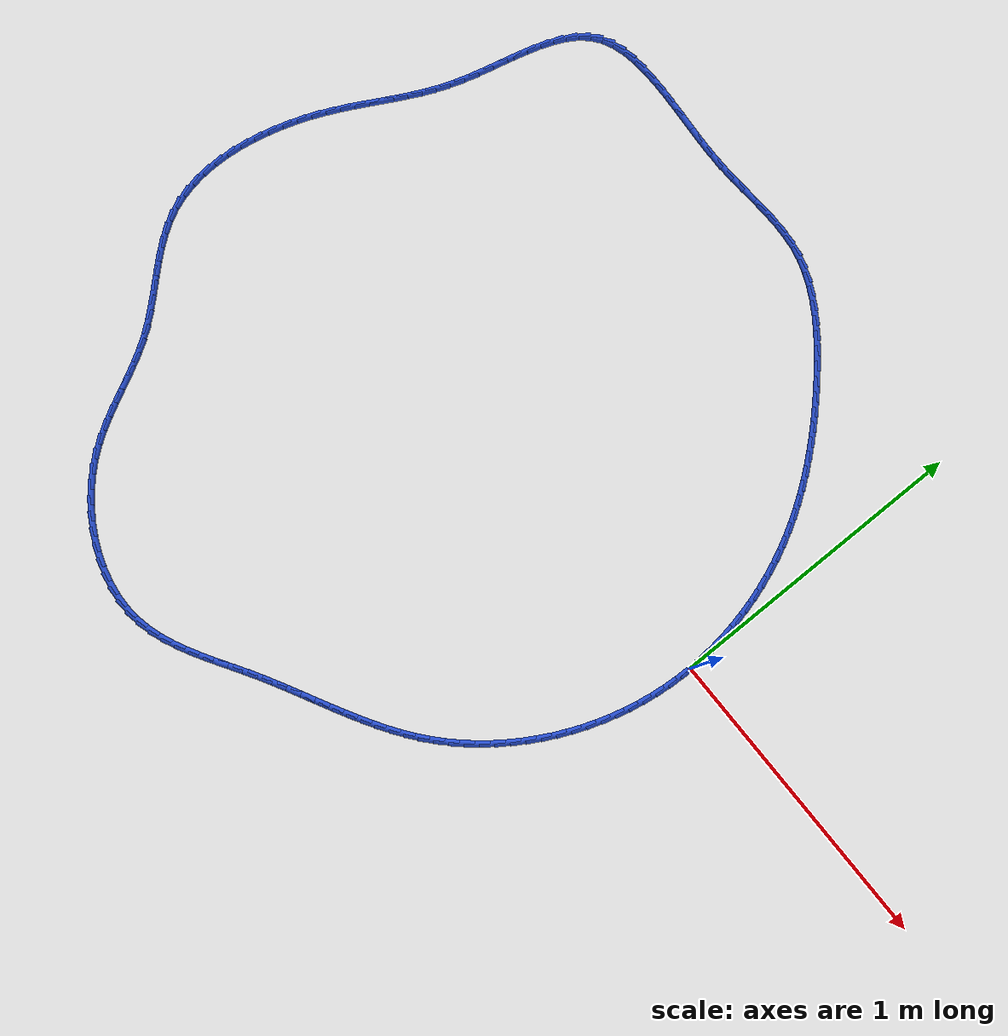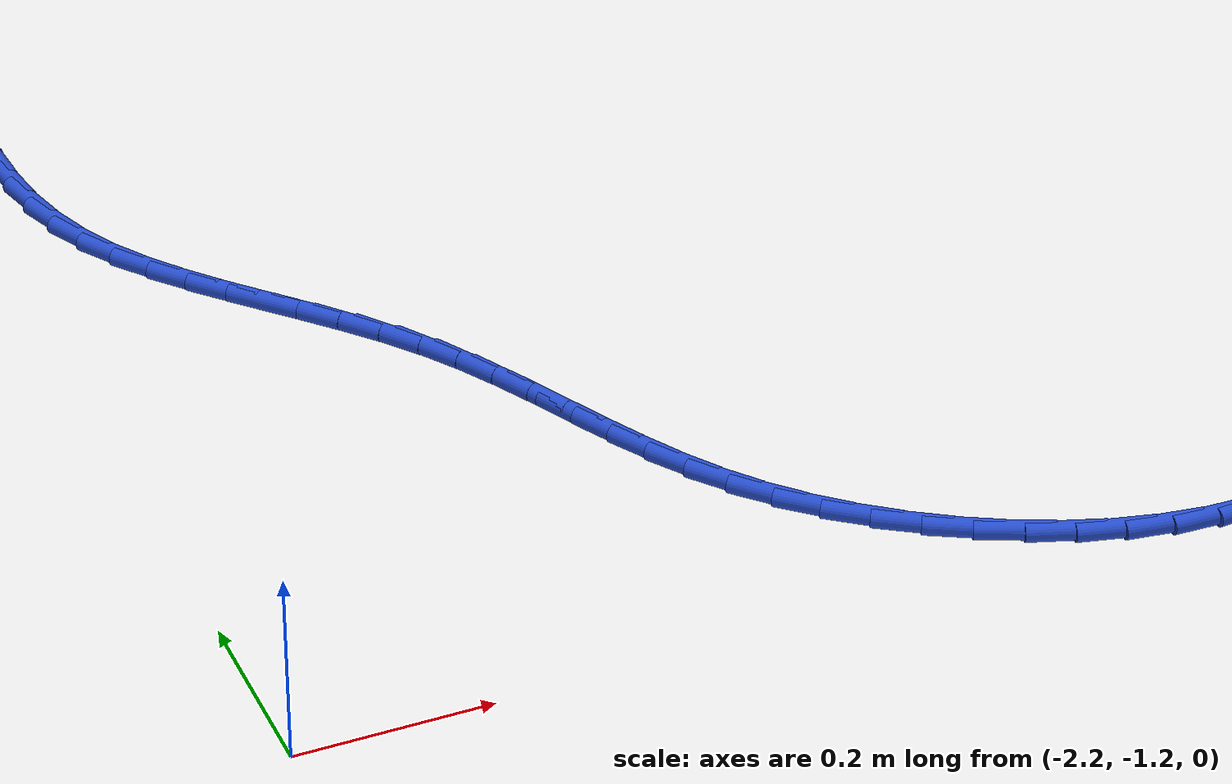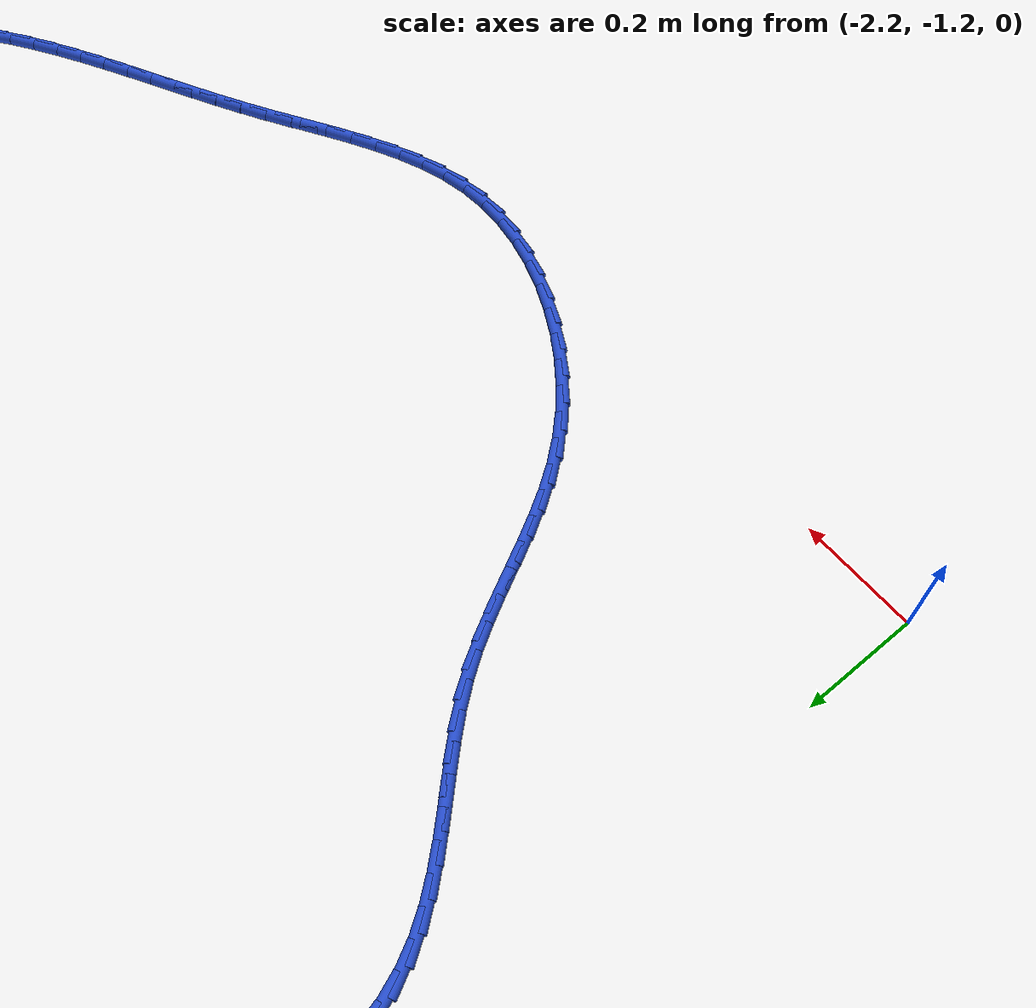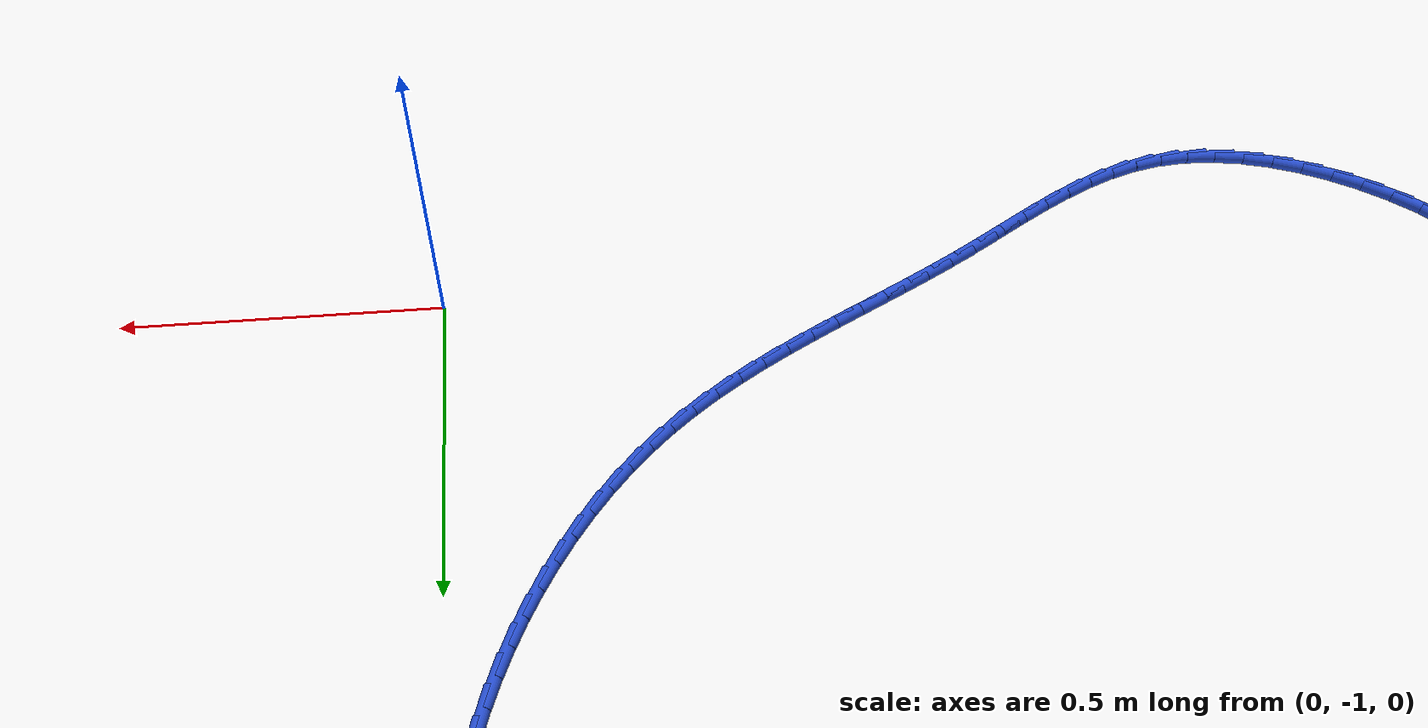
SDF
<sdf version="1.6">
 <world name="default">
  <light name="sun" type="directional">
   <pose>0 0 10 0 -0 0</pose>
   <diffuse>0.8 0.8 0.8 1</diffuse>
   <specular>0.2 0.2 0.2 1</specular>
   <attenuation>
    <range>1000</range>
    <constant>0.9</constant>
    <linear>0.01</linear>
    <quadratic>0.001</quadratic>
   </attenuation>
   <direction>-0.5 0.1 -0.9</direction>
  </light>
  <model name="ground_plane">
   <static>1</static>
   <link name="link">
    <collision name="collision">
     <geometry><plane><normal>0 0 1</normal><size>100 100</size></plane></geometry>
     <surface><friction><ode><mu>100</mu><mu2>50</mu2></ode></friction></surface>
    </collision>
    <visual name="visual">
     <cast_shadows>0</cast_shadows>
     <geometry><plane><normal>0 0 1</normal><size>100 100</size></plane></geometry>
     <material>
      <script><uri>file://media/materials/scripts/gazebo.material</uri><name>Gazebo/WhiteGlow</name></script>
     </material>
    </visual>
   </link>
  </model>
  <gravity>0 0 -9.8</gravity>
  <magnetic_field>6e-06 2.3e-05 -4.2e-05</magnetic_field>
  <atmosphere type="adiabatic"/>
  <physics name="default_physics" default="0" type="ode">
   <max_step_size>0.001</max_step_size>
   <real_time_factor>1</real_time_factor>
   <real_time_update_rate>1000</real_time_update_rate>
  </physics>
  <scene><ambient>0.4 0.4 0.4 1</ambient><background>0.7 0.7 0.7 1</background><shadows>1</shadows></scene>
  <spherical_coordinates>
   <surface_model>EARTH_WGS84</surface_model>
   <latitude_deg>0</latitude_deg>
   <longitude_deg>0</longitude_deg>
   <elevation>0</elevation>
   <heading_deg>0</heading_deg>
  </spherical_coordinates>
  <model name="line">
   <link name="link_0">
    <pose>-3.122502256758253e-17 1.3877787807814457e-17 0.01 0 1.57 -1.5429689902392099</pose>
    <collision name="collision">
     <geometry><cylinder><radius>0.01</radius><length>0.08</length></cylinder></geometry>
    </collision>
    <visual name="visual">
     <material>
      <script><name>Gazebo/Blue</name><uri>file://media/materials/scripts/gazebo.material</uri></script>
     </material>
     <geometry><cylinder><radius>0.01</radius><length>0.08</length></cylinder></geometry>
    </visual>
   </link>
   <link name="link_1">
    <pose>-0.0012918215380092201 0.04641076852433082 0.01 0 1.57 -1.4957556351680719</pose>
    <collision name="collision">
     <geometry><cylinder><radius>0.01</radius><length>0.08</length></cylinder></geometry>
    </collision>
    <visual name="visual">
     <material>
      <script><name>Gazebo/Blue</name><uri>file://media/materials/scripts/gazebo.material</uri></script>
     </material>
     <geometry><cylinder><radius>0.01</radius><length>0.08</length></cylinder></geometry>
    </visual>
   </link>
   <link name="link_2">
    <pose>-0.004776711012445879 0.09276356301618625 0.01 0 1.57 -1.449606159220448</pose>
    <collision name="collision">
     <geometry><cylinder><radius>0.01</radius><length>0.08</length></cylinder></geometry>
    </collision>
    <visual name="visual">
     <material>
      <script><name>Gazebo/Blue</name><uri>file://media/materials/scripts/gazebo.material</uri></script>
     </material>
     <geometry><cylinder><radius>0.01</radius><length>0.08</length></cylinder></geometry>
    </visual>
   </link>
   <link name="link_3">
    <pose>-0.010400524770756297 0.13894102485700363 0.01 0 1.57 -1.404351630841077</pose>
    <collision name="collision">
     <geometry><cylinder><radius>0.01</radius><length>0.08</length></cylinder></geometry>
    </collision>
    <visual name="visual">
     <material>
      <script><name>Gazebo/Blue</name><uri>file://media/materials/scripts/gazebo.material</uri></script>
     </material>
     <geometry><cylinder><radius>0.01</radius><length>0.08</length></cylinder></geometry>
    </visual>
   </link>
   <link name="link_4">
    <pose>-0.018109119160386777 0.18482579542822042 0.01 0 1.57 -1.3598155134194914</pose>
    <collision name="collision">
     <geometry><cylinder><radius>0.01</radius><length>0.08</length></cylinder></geometry>
    </collision>
    <visual name="visual">
     <material>
      <script><name>Gazebo/Blue</name><uri>file://media/materials/scripts/gazebo.material</uri></script>
     </material>
     <geometry><cylinder><radius>0.01</radius><length>0.08</length></cylinder></geometry>
    </visual>
   </link>
   <link name="link_5">
    <pose>-0.0278483505287836 0.23030051611127378 0.01 0 1.57 -1.3158151938457348</pose>
    <collision name="collision">
     <geometry><cylinder><radius>0.01</radius><length>0.08</length></cylinder></geometry>
    </collision>
    <visual name="visual">
     <material>
      <script><name>Gazebo/Blue</name><uri>file://media/materials/scripts/gazebo.material</uri></script>
     </material>
     <geometry><cylinder><radius>0.01</radius><length>0.08</length></cylinder></geometry>
    </visual>
   </link>
   <link name="link_6">
    <pose>-0.039564075223393086 0.2752478282876013 0.01 0 1.57 -1.2721629169399251</pose>
    <collision name="collision">
     <geometry><cylinder><radius>0.01</radius><length>0.08</length></cylinder></geometry>
    </collision>
    <visual name="visual">
     <material>
      <script><name>Gazebo/Blue</name><uri>file://media/materials/scripts/gazebo.material</uri></script>
     </material>
     <geometry><cylinder><radius>0.01</radius><length>0.08</length></cylinder></geometry>
    </visual>
   </link>
   <link name="link_7">
    <pose>-0.053202149591661516 0.31955037333864017 0.01 0 1.57 -1.228666249508194</pose>
    <collision name="collision">
     <geometry><cylinder><radius>0.01</radius><length>0.08</length></cylinder></geometry>
    </collision>
    <visual name="visual">
     <material>
      <script><name>Gazebo/Blue</name><uri>file://media/materials/scripts/gazebo.material</uri></script>
     </material>
     <geometry><cylinder><radius>0.01</radius><length>0.08</length></cylinder></geometry>
    </visual>
   </link>
   <link name="link_8">
    <pose>-0.0687084299810352 0.3630907926458279 0.01 0 1.57 -1.1851281973826122</pose>
    <collision name="collision">
     <geometry><cylinder><radius>0.01</radius><length>0.08</length></cylinder></geometry>
    </collision>
    <visual name="visual">
     <material>
      <script><name>Gazebo/Blue</name><uri>file://media/materials/scripts/gazebo.material</uri></script>
     </material>
     <geometry><cylinder><radius>0.01</radius><length>0.08</length></cylinder></geometry>
    </visual>
   </link>
   <link name="link_9">
    <pose>-0.08602877273896042 0.40575172759060163 0.01 0 1.57 -1.1415876496653528</pose>
    <collision name="collision">
     <geometry><cylinder><radius>0.01</radius><length>0.08</length></cylinder></geometry>
    </collision>
    <visual name="visual">
     <material>
      <script><name>Gazebo/Blue</name><uri>file://media/materials/scripts/gazebo.material</uri></script>
     </material>
     <geometry><cylinder><radius>0.01</radius><length>0.08</length></cylinder></geometry>
    </visual>
   </link>
   <link name="link_10">
    <pose>-0.10510783155418714 0.4474396803785444 0.01 0 1.57 -1.0990227829262018</pose>
    <collision name="collision">
     <geometry><cylinder><radius>0.01</radius><length>0.08</length></cylinder></geometry>
    </collision>
    <visual name="visual">
     <material>
      <script><name>Gazebo/Blue</name><uri>file://media/materials/scripts/gazebo.material</uri></script>
     </material>
     <geometry><cylinder><radius>0.01</radius><length>0.08</length></cylinder></geometry>
    </visual>
   </link>
   <link name="link_11">
    <pose>-0.1258851002111187 0.48816352604187824 0.01 0 1.57 -1.0578667665606885</pose>
    <collision name="collision">
     <geometry><cylinder><radius>0.01</radius><length>0.08</length></cylinder></geometry>
    </collision>
    <visual name="visual">
     <material>
      <script><name>Gazebo/Blue</name><uri>file://media/materials/scripts/gazebo.material</uri></script>
     </material>
     <geometry><cylinder><radius>0.01</radius><length>0.08</length></cylinder></geometry>
    </visual>
   </link>
   <link name="link_12">
    <pose>-0.14829868895306622 0.5279595891550759 0.01 0 1.57 -1.0182707191301958</pose>
    <collision name="collision">
     <geometry><cylinder><radius>0.01</radius><length>0.08</length></cylinder></geometry>
    </collision>
    <visual name="visual">
     <material>
      <script><name>Gazebo/Blue</name><uri>file://media/materials/scripts/gazebo.material</uri></script>
     </material>
     <geometry><cylinder><radius>0.01</radius><length>0.08</length></cylinder></geometry>
    </visual>
   </link>
   <link name="link_13">
    <pose>-0.17228670800689308 0.5668641946189341 0.01 0 1.57 -0.9803551299865266</pose>
    <collision name="collision">
     <geometry><cylinder><radius>0.01</radius><length>0.08</length></cylinder></geometry>
    </collision>
    <visual name="visual">
     <material>
      <script><name>Gazebo/Blue</name><uri>file://media/materials/scripts/gazebo.material</uri></script>
     </material>
     <geometry><cylinder><radius>0.01</radius><length>0.08</length></cylinder></geometry>
    </visual>
   </link>
   <link name="link_14">
    <pose>-0.19778726759946275 0.6049136673342501 0.01 0 1.57 -0.9442107248380446</pose>
    <collision name="collision">
     <geometry><cylinder><radius>0.01</radius><length>0.08</length></cylinder></geometry>
    </collision>
    <visual name="visual">
     <material>
      <script><name>Gazebo/Blue</name><uri>file://media/materials/scripts/gazebo.material</uri></script>
     </material>
     <geometry><cylinder><radius>0.01</radius><length>0.08</length></cylinder></geometry>
    </visual>
   </link>
   <link name="link_15">
    <pose>-0.22473847795763863 0.6421443322018212 0.01 0 1.57 -0.909900440066162</pose>
    <collision name="collision">
     <geometry><cylinder><radius>0.01</radius><length>0.08</length></cylinder></geometry>
    </collision>
    <visual name="visual">
     <material>
      <script><name>Gazebo/Blue</name><uri>file://media/materials/scripts/gazebo.material</uri></script>
     </material>
     <geometry><cylinder><radius>0.01</radius><length>0.08</length></cylinder></geometry>
    </visual>
   </link>
   <link name="link_16">
    <pose>-0.25307844930828405 0.6785925141224436 0.01 0 1.57 -0.8774621844678899</pose>
    <collision name="collision">
     <geometry><cylinder><radius>0.01</radius><length>0.08</length></cylinder></geometry>
    </collision>
    <visual name="visual">
     <material>
      <script><name>Gazebo/Blue</name><uri>file://media/materials/scripts/gazebo.material</uri></script>
     </material>
     <geometry><cylinder><radius>0.01</radius><length>0.08</length></cylinder></geometry>
    </visual>
   </link>
   <link name="link_17">
    <pose>-0.2827452918782625 0.7142945379969149 0.01 0 1.57 -0.8469120747195975</pose>
    <collision name="collision">
     <geometry><cylinder><radius>0.01</radius><length>0.08</length></cylinder></geometry>
    </collision>
    <visual name="visual">
     <material>
      <script><name>Gazebo/Blue</name><uri>file://media/materials/scripts/gazebo.material</uri></script>
     </material>
     <geometry><cylinder><radius>0.01</radius><length>0.08</length></cylinder></geometry>
    </visual>
   </link>
   <link name="link_18">
    <pose>-0.3136771158944373 0.7492867287260317 0.01 0 1.57 -0.8182478704940331</pose>
    <collision name="collision">
     <geometry><cylinder><radius>0.01</radius><length>0.08</length></cylinder></geometry>
    </collision>
    <visual name="visual">
     <material>
      <script><name>Gazebo/Blue</name><uri>file://media/materials/scripts/gazebo.material</uri></script>
     </material>
     <geometry><cylinder><radius>0.01</radius><length>0.08</length></cylinder></geometry>
    </visual>
   </link>
   <link name="link_19">
    <pose>-0.3458120315836719 0.7836054112105914 0.01 0 1.57 -0.791452390213166</pose>
    <collision name="collision">
     <geometry><cylinder><radius>0.01</radius><length>0.08</length></cylinder></geometry>
    </collision>
    <visual name="visual">
     <material>
      <script><name>Gazebo/Blue</name><uri>file://media/materials/scripts/gazebo.material</uri></script>
     </material>
     <geometry><cylinder><radius>0.01</radius><length>0.08</length></cylinder></geometry>
    </visual>
   </link>
   <link name="link_20">
    <pose>-0.3790881491728298 0.8172869103513906 0.01 0 1.57 -0.7664967476595134</pose>
    <collision name="collision">
     <geometry><cylinder><radius>0.01</radius><length>0.08</length></cylinder></geometry>
    </collision>
    <visual name="visual">
     <material>
      <script><name>Gazebo/Blue</name><uri>file://media/materials/scripts/gazebo.material</uri></script>
     </material>
     <geometry><cylinder><radius>0.01</radius><length>0.08</length></cylinder></geometry>
    </visual>
   </link>
   <link name="link_21">
    <pose>-0.4134435788887743 0.8503675510492263 0.01 0 1.57 -0.7433139750297793</pose>
    <collision name="collision">
     <geometry><cylinder><radius>0.01</radius><length>0.08</length></cylinder></geometry>
    </collision>
    <visual name="visual">
     <material>
      <script><name>Gazebo/Blue</name><uri>file://media/materials/scripts/gazebo.material</uri></script>
     </material>
     <geometry><cylinder><radius>0.01</radius><length>0.08</length></cylinder></geometry>
    </visual>
   </link>
   <link name="link_22">
    <pose>-0.44881650836748194 0.8828818152418216 0.01 0 1.57 -0.7190530721349292</pose>
    <collision name="collision">
     <geometry><cylinder><radius>0.01</radius><length>0.08</length></cylinder></geometry>
    </collision>
    <visual name="visual">
     <material>
      <script><name>Gazebo/Blue</name><uri>file://media/materials/scripts/gazebo.material</uri></script>
     </material>
     <geometry><cylinder><radius>0.01</radius><length>0.08</length></cylinder></geometry>
    </visual>
   </link>
   <link name="link_23">
    <pose>-0.4851524385801649 0.9146900683290224 0.01 0 1.57 -0.6883678950188451</pose>
    <collision name="collision">
     <geometry><cylinder><radius>0.01</radius><length>0.08</length></cylinder></geometry>
    </collision>
    <visual name="visual">
     <material>
      <script><name>Gazebo/Blue</name><uri>file://media/materials/scripts/gazebo.material</uri></script>
     </material>
     <geometry><cylinder><radius>0.01</radius><length>0.08</length></cylinder></geometry>
    </visual>
   </link>
   <link name="link_24">
    <pose>-0.5224100852822178 0.9453380569496486 0.01 0 1.57 -0.6501098971615135</pose>
    <collision name="collision">
     <geometry><cylinder><radius>0.01</radius><length>0.08</length></cylinder></geometry>
    </collision>
    <visual name="visual">
     <material>
      <script><name>Gazebo/Blue</name><uri>file://media/materials/scripts/gazebo.material</uri></script>
     </material>
     <geometry><cylinder><radius>0.01</radius><length>0.08</length></cylinder></geometry>
    </visual>
   </link>
   <link name="link_25">
    <pose>-0.5605495530582921 0.9743384623716483 0.01 0 1.57 -0.6034325827201155</pose>
    <collision name="collision">
     <geometry><cylinder><radius>0.01</radius><length>0.08</length></cylinder></geometry>
    </collision>
    <visual name="visual">
     <material>
      <script><name>Gazebo/Blue</name><uri>file://media/materials/scripts/gazebo.material</uri></script>
     </material>
     <geometry><cylinder><radius>0.01</radius><length>0.08</length></cylinder></geometry>
    </visual>
   </link>
   <link name="link_26">
    <pose>-0.599530946493039 1.0012039658629688 0.01 0 1.57 -0.5472891287982019</pose>
    <collision name="collision">
     <geometry><cylinder><radius>0.01</radius><length>0.08</length></cylinder></geometry>
    </collision>
    <visual name="visual">
     <material>
      <script><name>Gazebo/Blue</name><uri>file://media/materials/scripts/gazebo.material</uri></script>
     </material>
     <geometry><cylinder><radius>0.01</radius><length>0.08</length></cylinder></geometry>
    </visual>
   </link>
   <link name="link_27">
    <pose>-0.6393143701711105 1.0254472486915585 0.01 0 1.57 -0.48049053275816206</pose>
    <collision name="collision">
     <geometry><cylinder><radius>0.01</radius><length>0.08</length></cylinder></geometry>
    </collision>
    <visual name="visual">
     <material>
      <script><name>Gazebo/Blue</name><uri>file://media/materials/scripts/gazebo.material</uri></script>
     </material>
     <geometry><cylinder><radius>0.01</radius><length>0.08</length></cylinder></geometry>
    </visual>
   </link>
   <link name="link_28">
    <pose>-0.6798599286771576 1.0465809921253642 0.01 0 1.57 -0.401831058567321</pose>
    <collision name="collision">
     <geometry><cylinder><radius>0.01</radius><length>0.08</length></cylinder></geometry>
    </collision>
    <visual name="visual">
     <material>
      <script><name>Gazebo/Blue</name><uri>file://media/materials/scripts/gazebo.material</uri></script>
     </material>
     <geometry><cylinder><radius>0.01</radius><length>0.08</length></cylinder></geometry>
    </visual>
   </link>
   <link name="link_29">
    <pose>-0.7211277265958319 1.064117877432334 0.01 0 1.57 -0.31032261865265476</pose>
    <collision name="collision">
     <geometry><cylinder><radius>0.01</radius><length>0.08</length></cylinder></geometry>
    </collision>
    <visual name="visual">
     <material>
      <script><name>Gazebo/Blue</name><uri>file://media/materials/scripts/gazebo.material</uri></script>
     </material>
     <geometry><cylinder><radius>0.01</radius><length>0.08</length></cylinder></geometry>
    </visual>
   </link>
   <link name="link_30">
    <pose>-0.7630778685117849 1.0775705858804163 0.01 0 1.57 -0.2071887860075463</pose>
    <collision name="collision">
     <geometry><cylinder><radius>0.01</radius><length>0.08</length></cylinder></geometry>
    </collision>
    <visual name="visual">
     <material>
      <script><name>Gazebo/Blue</name><uri>file://media/materials/scripts/gazebo.material</uri></script>
     </material>
     <geometry><cylinder><radius>0.01</radius><length>0.08</length></cylinder></geometry>
    </visual>
   </link>
   <link name="link_31">
    <pose>-0.8056770742396852 1.0865251634206432 0.01 0 1.57 -0.11083185208823877</pose>
    <collision name="collision">
     <geometry><cylinder><radius>0.01</radius><length>0.08</length></cylinder></geometry>
    </collision>
    <visual name="visual">
     <material>
      <script><name>Gazebo/Blue</name><uri>file://media/materials/scripts/gazebo.material</uri></script>
     </material>
     <geometry><cylinder><radius>0.01</radius><length>0.08</length></cylinder></geometry>
    </visual>
   </link>
   <link name="link_32">
    <pose>-0.848961907312422 1.0913422416555325 0.01 0 1.57 -0.034156010957570815</pose>
    <collision name="collision">
     <geometry><cylinder><radius>0.01</radius><length>0.08</length></cylinder></geometry>
    </collision>
    <visual name="visual">
     <material>
      <script><name>Gazebo/Blue</name><uri>file://media/materials/scripts/gazebo.material</uri></script>
     </material>
     <geometry><cylinder><radius>0.01</radius><length>0.08</length></cylinder></geometry>
    </visual>
   </link>
   <link name="link_33">
    <pose>-0.8930108518906228 1.092847363242956 0.01 0 1.57 0.021714615140851948</pose>
    <collision name="collision">
     <geometry><cylinder><radius>0.01</radius><length>0.08</length></cylinder></geometry>
    </collision>
    <visual name="visual">
     <material>
      <script><name>Gazebo/Blue</name><uri>file://media/materials/scripts/gazebo.material</uri></script>
     </material>
     <geometry><cylinder><radius>0.01</radius><length>0.08</length></cylinder></geometry>
    </visual>
   </link>
   <link name="link_34">
    <pose>-0.9379029623874819 1.0918723950953793 0.01 0 1.57 0.057194549323245185</pose>
    <collision name="collision">
     <geometry><cylinder><radius>0.01</radius><length>0.08</length></cylinder></geometry>
    </collision>
    <visual name="visual">
     <material>
      <script><name>Gazebo/Blue</name><uri>file://media/materials/scripts/gazebo.material</uri></script>
     </material>
     <geometry><cylinder><radius>0.01</radius><length>0.08</length></cylinder></geometry>
    </visual>
   </link>
   <link name="link_35">
    <pose>-0.9837172932161931 1.089249204125267 0.01 0 1.57 0.07333832554534546</pose>
    <collision name="collision">
     <geometry><cylinder><radius>0.01</radius><length>0.08</length></cylinder></geometry>
    </collision>
    <visual name="visual">
     <material>
      <script><name>Gazebo/Blue</name><uri>file://media/materials/scripts/gazebo.material</uri></script>
     </material>
     <geometry><cylinder><radius>0.01</radius><length>0.08</length></cylinder></geometry>
    </visual>
   </link>
   <link name="link_36">
    <pose>-1.0305328987899507 1.0858096572450848 0.01 0 1.57 0.07136765697515104</pose>
    <collision name="collision">
     <geometry><cylinder><radius>0.01</radius><length>0.08</length></cylinder></geometry>
    </collision>
    <visual name="visual">
     <material>
      <script><name>Gazebo/Blue</name><uri>file://media/materials/scripts/gazebo.material</uri></script>
     </material>
     <geometry><cylinder><radius>0.01</radius><length>0.08</length></cylinder></geometry>
    </visual>
   </link>
   <link name="link_37">
    <pose>-1.0784288335219487 1.0823856213672975 0.01 0 1.57 0.05247733287333691</pose>
    <collision name="collision">
     <geometry><cylinder><radius>0.01</radius><length>0.08</length></cylinder></geometry>
    </collision>
    <visual name="visual">
     <material>
      <script><name>Gazebo/Blue</name><uri>file://media/materials/scripts/gazebo.material</uri></script>
     </material>
     <geometry><cylinder><radius>0.01</radius><length>0.08</length></cylinder></geometry>
    </visual>
   </link>
   <link name="link_38">
    <pose>-1.1274841518253818 1.0798089634043708 0.01 0 1.57 0.01790679159937567</pose>
    <collision name="collision">
     <geometry><cylinder><radius>0.01</radius><length>0.08</length></cylinder></geometry>
    </collision>
    <visual name="visual">
     <material>
      <script><name>Gazebo/Blue</name><uri>file://media/materials/scripts/gazebo.material</uri></script>
     </material>
     <geometry><cylinder><radius>0.01</radius><length>0.08</length></cylinder></geometry>
    </visual>
   </link>
   <link name="link_39">
    <pose>-1.177776668529454 1.0789082895187014 0.01 0 1.57 -0.02198568389857712</pose>
    <collision name="collision">
     <geometry><cylinder><radius>0.01</radius><length>0.08</length></cylinder></geometry>
    </collision>
    <visual name="visual">
     <material>
      <script><name>Gazebo/Blue</name><uri>file://media/materials/scripts/gazebo.material</uri></script>
     </material>
     <geometry><cylinder><radius>0.01</radius><length>0.08</length></cylinder></geometry>
    </visual>
   </link>
   <link name="link_40">
    <pose>-1.2292043628532534 1.0800391447628872 0.01 0 1.57 -0.048979455826992195</pose>
    <collision name="collision">
     <geometry><cylinder><radius>0.01</radius><length>0.08</length></cylinder></geometry>
    </collision>
    <visual name="visual">
     <material>
      <script><name>Gazebo/Blue</name><uri>file://media/materials/scripts/gazebo.material</uri></script>
     </material>
     <geometry><cylinder><radius>0.01</radius><length>0.08</length></cylinder></geometry>
    </visual>
   </link>
   <link name="link_41">
    <pose>-1.2812986176939245 1.0825927353536438 0.01 0 1.57 -0.06212567756247998</pose>
    <collision name="collision">
     <geometry><cylinder><radius>0.01</radius><length>0.08</length></cylinder></geometry>
    </collision>
    <visual name="visual">
     <material>
      <script><name>Gazebo/Blue</name><uri>file://media/materials/scripts/gazebo.material</uri></script>
     </material>
     <geometry><cylinder><radius>0.01</radius><length>0.08</length></cylinder></geometry>
    </visual>
   </link>
   <link name="link_42">
    <pose>-1.3335461726921143 1.0858428325433442 0.01 0 1.57 -0.06198494316220264</pose>
    <collision name="collision">
     <geometry><cylinder><radius>0.01</radius><length>0.08</length></cylinder></geometry>
    </collision>
    <visual name="visual">
     <material>
      <script><name>Gazebo/Blue</name><uri>file://media/materials/scripts/gazebo.material</uri></script>
     </material>
     <geometry><cylinder><radius>0.01</radius><length>0.08</length></cylinder></geometry>
    </visual>
   </link>
   <link name="link_43">
    <pose>-1.3854337674884754 1.0890632075843631 0.01 0 1.57 -0.04827089977322443</pose>
    <collision name="collision">
     <geometry><cylinder><radius>0.01</radius><length>0.08</length></cylinder></geometry>
    </collision>
    <visual name="visual">
     <material>
      <script><name>Gazebo/Blue</name><uri>file://media/materials/scripts/gazebo.material</uri></script>
     </material>
     <geometry><cylinder><radius>0.01</radius><length>0.08</length></cylinder></geometry>
    </visual>
   </link>
   <link name="link_44">
    <pose>-1.4364481417236559 1.0915276317290739 0.01 0 1.57 -0.019789602316324678</pose>
    <collision name="collision">
     <geometry><cylinder><radius>0.01</radius><length>0.08</length></cylinder></geometry>
    </collision>
    <visual name="visual">
     <material>
      <script><name>Gazebo/Blue</name><uri>file://media/materials/scripts/gazebo.material</uri></script>
     </material>
     <geometry><cylinder><radius>0.01</radius><length>0.08</length></cylinder></geometry>
    </visual>
   </link>
   <link name="link_45">
    <pose>-1.4860760350383078 1.09250987622985 0.01 0 1.57 0.025684929896435556</pose>
    <collision name="collision">
     <geometry><cylinder><radius>0.01</radius><length>0.08</length></cylinder></geometry>
    </collision>
    <visual name="visual">
     <material>
      <script><name>Gazebo/Blue</name><uri>file://media/materials/scripts/gazebo.material</uri></script>
     </material>
     <geometry><cylinder><radius>0.01</radius><length>0.08</length></cylinder></geometry>
    </visual>
   </link>
   <link name="link_46">
    <pose>-1.5338041870730794 1.0912837123390653 0.01 0 1.57 0.0915624658523891</pose>
    <collision name="collision">
     <geometry><cylinder><radius>0.01</radius><length>0.08</length></cylinder></geometry>
    </collision>
    <visual name="visual">
     <material>
      <script><name>Gazebo/Blue</name><uri>file://media/materials/scripts/gazebo.material</uri></script>
     </material>
     <geometry><cylinder><radius>0.01</radius><length>0.08</length></cylinder></geometry>
    </visual>
   </link>
   <link name="link_47">
    <pose>-1.5791193374686214 1.0871229113090934 0.01 0 1.57 0.18246919020248475</pose>
    <collision name="collision">
     <geometry><cylinder><radius>0.01</radius><length>0.08</length></cylinder></geometry>
    </collision>
    <visual name="visual">
     <material>
      <script><name>Gazebo/Blue</name><uri>file://media/materials/scripts/gazebo.material</uri></script>
     </material>
     <geometry><cylinder><radius>0.01</radius><length>0.08</length></cylinder></geometry>
    </visual>
   </link>
   <link name="link_48">
    <pose>-1.6215082258655835 1.079301244392308 0.01 0 1.57 0.3037520494369437</pose>
    <collision name="collision">
     <geometry><cylinder><radius>0.01</radius><length>0.08</length></cylinder></geometry>
    </collision>
    <visual name="visual">
     <material>
      <script><name>Gazebo/Blue</name><uri>file://media/materials/scripts/gazebo.material</uri></script>
     </material>
     <geometry><cylinder><radius>0.01</radius><length>0.08</length></cylinder></geometry>
    </visual>
   </link>
   <link name="link_49">
    <pose>-1.6604575919046156 1.0670924828410824 0.01 0 1.57 0.4596115266989873</pose>
    <collision name="collision">
     <geometry><cylinder><radius>0.01</radius><length>0.08</length></cylinder></geometry>
    </collision>
    <visual name="visual">
     <material>
      <script><name>Gazebo/Blue</name><uri>file://media/materials/scripts/gazebo.material</uri></script>
     </material>
     <geometry><cylinder><radius>0.01</radius><length>0.08</length></cylinder></geometry>
    </visual>
   </link>
   <link name="link_50">
    <pose>-1.6954541752263688 1.049770397907791 0.01 0 1.57 0.649001968652304</pose>
    <collision name="collision">
     <geometry><cylinder><radius>0.01</radius><length>0.08</length></cylinder></geometry>
    </collision>
    <visual name="visual">
     <material>
      <script><name>Gazebo/Blue</name><uri>file://media/materials/scripts/gazebo.material</uri></script>
     </material>
     <geometry><cylinder><radius>0.01</radius><length>0.08</length></cylinder></geometry>
    </visual>
   </link>
   <link name="link_51">
    <pose>-1.7259848262118644 1.0266089060878925 0.01 0 1.57 0.8500088046293869</pose>
    <collision name="collision">
     <geometry><cylinder><radius>0.01</radius><length>0.08</length></cylinder></geometry>
    </collision>
    <visual name="visual">
     <material>
      <script><name>Gazebo/Blue</name><uri>file://media/materials/scripts/gazebo.material</uri></script>
     </material>
     <geometry><cylinder><radius>0.01</radius><length>0.08</length></cylinder></geometry>
    </visual>
   </link>
   <link name="link_52">
    <pose>-1.7517977423956759 0.9972246973927744 0.01 0 1.57 1.015436989228022</pose>
    <collision name="collision">
     <geometry><cylinder><radius>0.01</radius><length>0.08</length></cylinder></geometry>
    </collision>
    <visual name="visual">
     <material>
      <script><name>Gazebo/Blue</name><uri>file://media/materials/scripts/gazebo.material</uri></script>
     </material>
     <geometry><cylinder><radius>0.01</radius><length>0.08</length></cylinder></geometry>
    </visual>
   </link>
   <link name="link_53">
    <pose>-1.7734618641705988 0.96231091861311 0.01 0 1.57 1.138472140044727</pose>
    <collision name="collision">
     <geometry><cylinder><radius>0.01</radius><length>0.08</length></cylinder></geometry>
    </collision>
    <visual name="visual">
     <material>
      <script><name>Gazebo/Blue</name><uri>file://media/materials/scripts/gazebo.material</uri></script>
     </material>
     <geometry><cylinder><radius>0.01</radius><length>0.08</length></cylinder></geometry>
    </visual>
   </link>
   <link name="link_54">
    <pose>-1.7917068273969143 0.9227714789283563 0.01 0 1.57 1.225621178700942</pose>
    <collision name="collision">
     <geometry><cylinder><radius>0.01</radius><length>0.08</length></cylinder></geometry>
    </collision>
    <visual name="visual">
     <material>
      <script><name>Gazebo/Blue</name><uri>file://media/materials/scripts/gazebo.material</uri></script>
     </material>
     <geometry><cylinder><radius>0.01</radius><length>0.08</length></cylinder></geometry>
    </visual>
   </link>
   <link name="link_55">
    <pose>-1.807262267934905 0.8795102875179723 0.01 0 1.57 1.283888283617322</pose>
    <collision name="collision">
     <geometry><cylinder><radius>0.01</radius><length>0.08</length></cylinder></geometry>
    </collision>
    <visual name="visual">
     <material>
      <script><name>Gazebo/Blue</name><uri>file://media/materials/scripts/gazebo.material</uri></script>
     </material>
     <geometry><cylinder><radius>0.01</radius><length>0.08</length></cylinder></geometry>
    </visual>
   </link>
   <link name="link_56">
    <pose>-1.8208578216448532 0.8334312535614155 0.01 0 1.57 1.318632390605863</pose>
    <collision name="collision">
     <geometry><cylinder><radius>0.01</radius><length>0.08</length></cylinder></geometry>
    </collision>
    <visual name="visual">
     <material>
      <script><name>Gazebo/Blue</name><uri>file://media/materials/scripts/gazebo.material</uri></script>
     </material>
     <geometry><cylinder><radius>0.01</radius><length>0.08</length></cylinder></geometry>
    </visual>
   </link>
   <link name="link_57">
    <pose>-1.833223124387041 0.7854382862381437 0.01 0 1.57 1.333246167731175</pose>
    <collision name="collision">
     <geometry><cylinder><radius>0.01</radius><length>0.08</length></cylinder></geometry>
    </collision>
    <visual name="visual">
     <material>
      <script><name>Gazebo/Blue</name><uri>file://media/materials/scripts/gazebo.material</uri></script>
     </material>
     <geometry><cylinder><radius>0.01</radius><length>0.08</length></cylinder></geometry>
    </visual>
   </link>
   <link name="link_58">
    <pose>-1.8450878120217507 0.7364352947276149 0.01 0 1.57 1.3293388330928213</pose>
    <collision name="collision">
     <geometry><cylinder><radius>0.01</radius><length>0.08</length></cylinder></geometry>
    </collision>
    <visual name="visual">
     <material>
      <script><name>Gazebo/Blue</name><uri>file://media/materials/scripts/gazebo.material</uri></script>
     </material>
     <geometry><cylinder><radius>0.01</radius><length>0.08</length></cylinder></geometry>
    </visual>
   </link>
   <link name="link_59">
    <pose>-1.857181520409264 0.6873261882092875 0.01 0 1.57 1.306924164472384</pose>
    <collision name="collision">
     <geometry><cylinder><radius>0.01</radius><length>0.08</length></cylinder></geometry>
    </collision>
    <visual name="visual">
     <material>
      <script><name>Gazebo/Blue</name><uri>file://media/materials/scripts/gazebo.material</uri></script>
     </material>
     <geometry><cylinder><radius>0.01</radius><length>0.08</length></cylinder></geometry>
    </visual>
   </link>
   <link name="link_60">
    <pose>-1.870233885409863 0.639014875862619 0.01 0 1.57 1.264588774454825</pose>
    <collision name="collision">
     <geometry><cylinder><radius>0.01</radius><length>0.08</length></cylinder></geometry>
    </collision>
    <visual name="visual">
     <material>
      <script><name>Gazebo/Blue</name><uri>file://media/materials/scripts/gazebo.material</uri></script>
     </material>
     <geometry><cylinder><radius>0.01</radius><length>0.08</length></cylinder></geometry>
    </visual>
   </link>
   <link name="link_61">
    <pose>-1.884970935100629 0.592400912514437 0.01 0 1.57 1.20984001735704</pose>
    <collision name="collision">
     <geometry><cylinder><radius>0.01</radius><length>0.08</length></cylinder></geometry>
    </collision>
    <visual name="visual">
     <material>
      <script><name>Gazebo/Blue</name><uri>file://media/materials/scripts/gazebo.material</uri></script>
     </material>
     <geometry><cylinder><radius>0.01</radius><length>0.08</length></cylinder></geometry>
    </visual>
   </link>
   <link name="link_62">
    <pose>-1.9017535309242093 0.54794312132722 0.01 0 1.57 1.161276306738726</pose>
    <collision name="collision">
     <geometry><cylinder><radius>0.01</radius><length>0.08</length></cylinder></geometry>
    </collision>
    <visual name="visual">
     <material>
      <script><name>Gazebo/Blue</name><uri>file://media/materials/scripts/gazebo.material</uri></script>
     </material>
     <geometry><cylinder><radius>0.01</radius><length>0.08</length></cylinder></geometry>
    </visual>
   </link>
   <link name="link_63">
    <pose>-1.9202688003023838 0.5052871736353618 0.01 0 1.57 1.1224846416783973</pose>
    <collision name="collision">
     <geometry><cylinder><radius>0.01</radius><length>0.08</length></cylinder></geometry>
    </collision>
    <visual name="visual">
     <material>
      <script><name>Gazebo/Blue</name><uri>file://media/materials/scripts/gazebo.material</uri></script>
     </material>
     <geometry><cylinder><radius>0.01</radius><length>0.08</length></cylinder></geometry>
    </visual>
   </link>
   <link name="link_64">
    <pose>-1.940131194246929 0.4639910252151494 0.01 0 1.57 1.094651472980846</pose>
    <collision name="collision">
     <geometry><cylinder><radius>0.01</radius><length>0.08</length></cylinder></geometry>
    </collision>
    <visual name="visual">
     <material>
      <script><name>Gazebo/Blue</name><uri>file://media/materials/scripts/gazebo.material</uri></script>
     </material>
     <geometry><cylinder><radius>0.01</radius><length>0.08</length></cylinder></geometry>
    </visual>
   </link>
   <link name="link_65">
    <pose>-1.9609551637696188 0.4236126318428695 0.01 0 1.57 1.078528509126694</pose>
    <collision name="collision">
     <geometry><cylinder><radius>0.01</radius><length>0.08</length></cylinder></geometry>
    </collision>
    <visual name="visual">
     <material>
      <script><name>Gazebo/Blue</name><uri>file://media/materials/scripts/gazebo.material</uri></script>
     </material>
     <geometry><cylinder><radius>0.01</radius><length>0.08</length></cylinder></geometry>
    </visual>
   </link>
   <link name="link_66">
    <pose>-1.9823551598822284 0.38370994929480917 0.01 0 1.57 1.0744752581298518</pose>
    <collision name="collision">
     <geometry><cylinder><radius>0.01</radius><length>0.08</length></cylinder></geometry>
    </collision>
    <visual name="visual">
     <material>
      <script><name>Gazebo/Blue</name><uri>file://media/materials/scripts/gazebo.material</uri></script>
     </material>
     <geometry><cylinder><radius>0.01</radius><length>0.08</length></cylinder></geometry>
    </visual>
   </link>
   <link name="link_67">
    <pose>-2.0039456335965324 0.343840933347255 0.01 0 1.57 1.0825003863119556</pose>
    <collision name="collision">
     <geometry><cylinder><radius>0.01</radius><length>0.08</length></cylinder></geometry>
    </collision>
    <visual name="visual">
     <material>
      <script><name>Gazebo/Blue</name><uri>file://media/materials/scripts/gazebo.material</uri></script>
     </material>
     <geometry><cylinder><radius>0.01</radius><length>0.08</length></cylinder></geometry>
    </visual>
   </link>
   <link name="link_68">
    <pose>-2.025341035924305 0.30356353977649464 0.01 0 1.57 1.102280739569995</pose>
    <collision name="collision">
     <geometry><cylinder><radius>0.01</radius><length>0.08</length></cylinder></geometry>
    </collision>
    <visual name="visual">
     <material>
      <script><name>Gazebo/Blue</name><uri>file://media/materials/scripts/gazebo.material</uri></script>
     </material>
     <geometry><cylinder><radius>0.01</radius><length>0.08</length></cylinder></geometry>
    </visual>
   </link>
   <link name="link_69">
    <pose>-2.0461558178773225 0.2624357243588149 0.01 0 1.57 1.1331537219815495</pose>
    <collision name="collision">
     <geometry><cylinder><radius>0.01</radius><length>0.08</length></cylinder></geometry>
    </collision>
    <visual name="visual">
     <material>
      <script><name>Gazebo/Blue</name><uri>file://media/materials/scripts/gazebo.material</uri></script>
     </material>
     <geometry><cylinder><radius>0.01</radius><length>0.08</length></cylinder></geometry>
    </visual>
   </link>
   <link name="link_70">
    <pose>-2.0660044304673577 0.22001544287050268 0.01 0 1.57 1.173227146026849</pose>
    <collision name="collision">
     <geometry><cylinder><radius>0.01</radius><length>0.08</length></cylinder></geometry>
    </collision>
    <visual name="visual">
     <material>
      <script><name>Gazebo/Blue</name><uri>file://media/materials/scripts/gazebo.material</uri></script>
     </material>
     <geometry><cylinder><radius>0.01</radius><length>0.08</length></cylinder></geometry>
    </visual>
   </link>
   <link name="link_71">
    <pose>-2.0845113708223955 0.17594403963600624 0.01 0 1.57 1.2166216404447607</pose>
    <collision name="collision">
     <geometry><cylinder><radius>0.01</radius><length>0.08</length></cylinder></geometry>
    </collision>
    <visual name="visual">
     <material>
      <script><name>Gazebo/Blue</name><uri>file://media/materials/scripts/gazebo.material</uri></script>
     </material>
     <geometry><cylinder><radius>0.01</radius><length>0.08</length></cylinder></geometry>
    </visual>
   </link>
   <link name="link_72">
    <pose>-2.101362454178282 0.13037183457639345 0.01 0 1.57 1.262057430843992</pose>
    <collision name="collision">
     <geometry><cylinder><radius>0.01</radius><length>0.08</length></cylinder></geometry>
    </collision>
    <visual name="visual">
     <material>
      <script><name>Gazebo/Blue</name><uri>file://media/materials/scripts/gazebo.material</uri></script>
     </material>
     <geometry><cylinder><radius>0.01</radius><length>0.08</length></cylinder></geometry>
    </visual>
   </link>
   <link name="link_73">
    <pose>-2.1162666263596805 0.08364114481636611 0.01 0 1.57 1.3104456474203467</pose>
    <collision name="collision">
     <geometry><cylinder><radius>0.01</radius><length>0.08</length></cylinder></geometry>
    </collision>
    <visual name="visual">
     <material>
      <script><name>Gazebo/Blue</name><uri>file://media/materials/scripts/gazebo.material</uri></script>
     </material>
     <geometry><cylinder><radius>0.01</radius><length>0.08</length></cylinder></geometry>
    </visual>
   </link>
   <link name="link_74">
    <pose>-2.12893287578692 0.03609464104920041 0.01 0 1.57 1.3627434985737172</pose>
    <collision name="collision">
     <geometry><cylinder><radius>0.01</radius><length>0.08</length></cylinder></geometry>
    </collision>
    <visual name="visual">
     <material>
      <script><name>Gazebo/Blue</name><uri>file://media/materials/scripts/gazebo.material</uri></script>
     </material>
     <geometry><cylinder><radius>0.01</radius><length>0.08</length></cylinder></geometry>
    </visual>
   </link>
   <link name="link_75">
    <pose>-2.139070190880333 -0.01192500603182736 0.01 0 1.57 1.4199803794109818</pose>
    <collision name="collision">
     <geometry><cylinder><radius>0.01</radius><length>0.08</length></cylinder></geometry>
    </collision>
    <visual name="visual">
     <material>
      <script><name>Gazebo/Blue</name><uri>file://media/materials/scripts/gazebo.material</uri></script>
     </material>
     <geometry><cylinder><radius>0.01</radius><length>0.08</length></cylinder></geometry>
    </visual>
   </link>
   <link name="link_76">
    <pose>-2.14638756006025 -0.06007512573344158 0.01 0 1.57 1.4832734362642437</pose>
    <collision name="collision">
     <geometry><cylinder><radius>0.01</radius><length>0.08</length></cylinder></geometry>
    </collision>
    <visual name="visual">
     <material>
      <script><name>Gazebo/Blue</name><uri>file://media/materials/scripts/gazebo.material</uri></script>
     </material>
     <geometry><cylinder><radius>0.01</radius><length>0.08</length></cylinder></geometry>
    </visual>
   </link>
   <link name="link_77">
    <pose>-2.1505939717470017 -0.10801304736236544 0.01 0 1.57 1.5538205244848378</pose>
    <collision name="collision">
     <geometry><cylinder><radius>0.01</radius><length>0.08</length></cylinder></geometry>
    </collision>
    <visual name="visual">
     <material>
      <script><name>Gazebo/Blue</name><uri>file://media/materials/scripts/gazebo.material</uri></script>
     </material>
     <geometry><cylinder><radius>0.01</radius><length>0.08</length></cylinder></geometry>
    </visual>
   </link>
   <link name="link_78">
    <pose>-2.1513984143609197 -0.1553961002253221 0.01 0 1.57 -1.5087376619041846</pose>
    <collision name="collision">
     <geometry><cylinder><radius>0.01</radius><length>0.08</length></cylinder></geometry>
    </collision>
    <visual name="visual">
     <material>
      <script><name>Gazebo/Blue</name><uri>file://media/materials/scripts/gazebo.material</uri></script>
     </material>
     <geometry><cylinder><radius>0.01</radius><length>0.08</length></cylinder></geometry>
    </visual>
   </link>
   <link name="link_79">
    <pose>-2.1485098763223336 -0.20188161362903673 0.01 0 1.57 -1.4200537050922653</pose>
    <collision name="collision">
     <geometry><cylinder><radius>0.01</radius><length>0.08</length></cylinder></geometry>
    </collision>
    <visual name="visual">
     <material>
      <script><name>Gazebo/Blue</name><uri>file://media/materials/scripts/gazebo.material</uri></script>
     </material>
     <geometry><cylinder><radius>0.01</radius><length>0.08</length></cylinder></geometry>
    </visual>
   </link>
   <link name="link_80">
    <pose>-2.1416373460515747 -0.2471269168802317 0.01 0 1.57 -1.3208245523780549</pose>
    <collision name="collision">
     <geometry><cylinder><radius>0.01</radius><length>0.08</length></cylinder></geometry>
    </collision>
    <visual name="visual">
     <material>
      <script><name>Gazebo/Blue</name><uri>file://media/materials/scripts/gazebo.material</uri></script>
     </material>
     <geometry><cylinder><radius>0.01</radius><length>0.08</length></cylinder></geometry>
    </visual>
   </link>
   <link name="link_81">
    <pose>-2.130489811968975 -0.2907893392856323 0.01 0 1.57 -1.2107192618182852</pose>
    <collision name="collision">
     <geometry><cylinder><radius>0.01</radius><length>0.08</length></cylinder></geometry>
    </collision>
    <visual name="visual">
     <material>
      <script><name>Gazebo/Blue</name><uri>file://media/materials/scripts/gazebo.material</uri></script>
     </material>
     <geometry><cylinder><radius>0.01</radius><length>0.08</length></cylinder></geometry>
    </visual>
   </link>
   <link name="link_82">
    <pose>-2.114776262494865 -0.3325262101519615 0.01 0 1.57 -1.092602460139994</pose>
    <collision name="collision">
     <geometry><cylinder><radius>0.01</radius><length>0.08</length></cylinder></geometry>
    </collision>
    <visual name="visual">
     <material>
      <script><name>Gazebo/Blue</name><uri>file://media/materials/scripts/gazebo.material</uri></script>
     </material>
     <geometry><cylinder><radius>0.01</radius><length>0.08</length></cylinder></geometry>
    </visual>
   </link>
   <link name="link_83">
    <pose>-2.0942898842576088 -0.3720509891239041 0.01 0 1.57 -0.9882693294790715</pose>
    <collision name="collision">
     <geometry><cylinder><radius>0.01</radius><length>0.08</length></cylinder></geometry>
    </collision>
    <visual name="visual">
     <material>
      <script><name>Gazebo/Blue</name><uri>file://media/materials/scripts/gazebo.material</uri></script>
     </material>
     <geometry><cylinder><radius>0.01</radius><length>0.08</length></cylinder></geometry>
    </visual>
   </link>
   <link name="link_84">
    <pose>-2.0695699209130716 -0.40957449124205764 0.01 0 1.57 -0.9092339965619007</pose>
    <collision name="collision">
     <geometry><cylinder><radius>0.01</radius><length>0.08</length></cylinder></geometry>
    </collision>
    <visual name="visual">
     <material>
      <script><name>Gazebo/Blue</name><uri>file://media/materials/scripts/gazebo.material</uri></script>
     </material>
     <geometry><cylinder><radius>0.01</radius><length>0.08</length></cylinder></geometry>
    </visual>
   </link>
   <link name="link_85">
    <pose>-2.0415454331595813 -0.4455674012383985 0.01 0 1.57 -0.8547583693760171</pose>
    <collision name="collision">
     <geometry><cylinder><radius>0.01</radius><length>0.08</length></cylinder></geometry>
    </collision>
    <visual name="visual">
     <material>
      <script><name>Gazebo/Blue</name><uri>file://media/materials/scripts/gazebo.material</uri></script>
     </material>
     <geometry><cylinder><radius>0.01</radius><length>0.08</length></cylinder></geometry>
    </visual>
   </link>
   <link name="link_86">
    <pose>-2.0111488766470327 -0.4805026670733416 0.01 0 1.57 -0.8233693868195241</pose>
    <collision name="collision">
     <geometry><cylinder><radius>0.01</radius><length>0.08</length></cylinder></geometry>
    </collision>
    <visual name="visual">
     <material>
      <script><name>Gazebo/Blue</name><uri>file://media/materials/scripts/gazebo.material</uri></script>
     </material>
     <geometry><cylinder><radius>0.01</radius><length>0.08</length></cylinder></geometry>
    </visual>
   </link>
   <link name="link_87">
    <pose>-1.9793127070253205 -0.5148532367073001 0.01 0 1.57 -0.8138589825990505</pose>
    <collision name="collision">
     <geometry><cylinder><radius>0.01</radius><length>0.08</length></cylinder></geometry>
    </collision>
    <visual name="visual">
     <material>
      <script><name>Gazebo/Blue</name><uri>file://media/materials/scripts/gazebo.material</uri></script>
     </material>
     <geometry><cylinder><radius>0.01</radius><length>0.08</length></cylinder></geometry>
    </visual>
   </link>
   <link name="link_88">
    <pose>-1.9469693799443388 -0.5490920581006871 0.01 0 1.57 -0.8256961018040806</pose>
    <collision name="collision">
     <geometry><cylinder><radius>0.01</radius><length>0.08</length></cylinder></geometry>
    </collision>
    <visual name="visual">
     <material>
      <script><name>Gazebo/Blue</name><uri>file://media/materials/scripts/gazebo.material</uri></script>
     </material>
     <geometry><cylinder><radius>0.01</radius><length>0.08</length></cylinder></geometry>
    </visual>
   </link>
   <link name="link_89">
    <pose>-1.9150513510539817 -0.5836920792139177 0.01 0 1.57 -0.8591174214775699</pose>
    <collision name="collision">
     <geometry><cylinder><radius>0.01</radius><length>0.08</length></cylinder></geometry>
    </collision>
    <visual name="visual">
     <material>
      <script><name>Gazebo/Blue</name><uri>file://media/materials/scripts/gazebo.material</uri></script>
     </material>
     <geometry><cylinder><radius>0.01</radius><length>0.08</length></cylinder></geometry>
    </visual>
   </link>
   <link name="link_90">
    <pose>-1.8844910760041436 -0.6191262480074049 0.01 0 1.57 -0.9149704807824931</pose>
    <collision name="collision">
     <geometry><cylinder><radius>0.01</radius><length>0.08</length></cylinder></geometry>
    </collision>
    <visual name="visual">
     <material>
      <script><name>Gazebo/Blue</name><uri>file://media/materials/scripts/gazebo.material</uri></script>
     </material>
     <geometry><cylinder><radius>0.01</radius><length>0.08</length></cylinder></geometry>
    </visual>
   </link>
   <link name="link_91">
    <pose>-1.8562209662392808 -0.6558674896075732 0.01 0 1.57 -0.9859981818546693</pose>
    <collision name="collision">
     <geometry><cylinder><radius>0.01</radius><length>0.08</length></cylinder></geometry>
    </collision>
    <visual name="visual">
     <material>
      <script><name>Gazebo/Blue</name><uri>file://media/materials/scripts/gazebo.material</uri></script>
     </material>
     <geometry><cylinder><radius>0.01</radius><length>0.08</length></cylinder></geometry>
    </visual>
   </link>
   <link name="link_92">
    <pose>-1.8308341044540744 -0.6942134514135393 0.01 0 1.57 -1.0438904494432948</pose>
    <collision name="collision">
     <geometry><cylinder><radius>0.01</radius><length>0.08</length></cylinder></geometry>
    </collision>
    <visual name="visual">
     <material>
      <script><name>Gazebo/Blue</name><uri>file://media/materials/scripts/gazebo.material</uri></script>
     </material>
     <geometry><cylinder><radius>0.01</radius><length>0.08</length></cylinder></geometry>
    </visual>
   </link>
   <link name="link_93">
    <pose>-1.8077665895946393 -0.733864149524038 0.01 0 1.57 -1.081926793127314</pose>
    <collision name="collision">
     <geometry><cylinder><radius>0.01</radius><length>0.08</length></cylinder></geometry>
    </collision>
    <visual name="visual">
     <material>
      <script><name>Gazebo/Blue</name><uri>file://media/materials/scripts/gazebo.material</uri></script>
     </material>
     <geometry><cylinder><radius>0.01</radius><length>0.08</length></cylinder></geometry>
    </visual>
   </link>
   <link name="link_94">
    <pose>-1.7862081489622976 -0.7743923386077 0.01 0 1.57 -1.0999433509527803</pose>
    <collision name="collision">
     <geometry><cylinder><radius>0.01</radius><length>0.08</length></cylinder></geometry>
    </collision>
    <visual name="visual">
     <material>
      <script><name>Gazebo/Blue</name><uri>file://media/materials/scripts/gazebo.material</uri></script>
     </material>
     <geometry><cylinder><radius>0.01</radius><length>0.08</length></cylinder></geometry>
    </visual>
   </link>
   <link name="link_95">
    <pose>-1.7653485098583743 -0.8153707733331547 0.01 0 1.57 -1.0980128240945162</pose>
    <collision name="collision">
     <geometry><cylinder><radius>0.01</radius><length>0.08</length></cylinder></geometry>
    </collision>
    <visual name="visual">
     <material>
      <script><name>Gazebo/Blue</name><uri>file://media/materials/scripts/gazebo.material</uri></script>
     </material>
     <geometry><cylinder><radius>0.01</radius><length>0.08</length></cylinder></geometry>
    </visual>
   </link>
   <link name="link_96">
    <pose>-1.744377399584192 -0.8563722083690302 0.01 0 1.57 -1.0762282834672172</pose>
    <collision name="collision">
     <geometry><cylinder><radius>0.01</radius><length>0.08</length></cylinder></geometry>
    </collision>
    <visual name="visual">
     <material>
      <script><name>Gazebo/Blue</name><uri>file://media/materials/scripts/gazebo.material</uri></script>
     </material>
     <geometry><cylinder><radius>0.01</radius><length>0.08</length></cylinder></geometry>
    </visual>
   </link>
   <link name="link_97">
    <pose>-1.7224845454410733 -0.8969693983839578 0.01 0 1.57 -1.0347250820600675</pose>
    <collision name="collision">
     <geometry><cylinder><radius>0.01</radius><length>0.08</length></cylinder></geometry>
    </collision>
    <visual name="visual">
     <material>
      <script><name>Gazebo/Blue</name><uri>file://media/materials/scripts/gazebo.material</uri></script>
     </material>
     <geometry><cylinder><radius>0.01</radius><length>0.08</length></cylinder></geometry>
    </visual>
   </link>
   <link name="link_98">
    <pose>-1.698859674730343 -0.9367350980465661 0.01 0 1.57 -0.9739318415360029</pose>
    <collision name="collision">
     <geometry><cylinder><radius>0.01</radius><length>0.08</length></cylinder></geometry>
    </collision>
    <visual name="visual">
     <material>
      <script><name>Gazebo/Blue</name><uri>file://media/materials/scripts/gazebo.material</uri></script>
     </material>
     <geometry><cylinder><radius>0.01</radius><length>0.08</length></cylinder></geometry>
    </visual>
   </link>
   <link name="link_99">
    <pose>-1.6726925147533227 -0.9752420620254849 0.01 0 1.57 -0.8952580154243821</pose>
    <collision name="collision">
     <geometry><cylinder><radius>0.01</radius><length>0.08</length></cylinder></geometry>
    </collision>
    <visual name="visual">
     <material>
      <script><name>Gazebo/Blue</name><uri>file://media/materials/scripts/gazebo.material</uri></script>
     </material>
     <geometry><cylinder><radius>0.01</radius><length>0.08</length></cylinder></geometry>
    </visual>
   </link>
   <link name="link_100">
    <pose>-1.6431866674633515 -1.0120641430836972 0.01 0 1.57 -0.8095339877894495</pose>
    <collision name="collision">
     <geometry><cylinder><radius>0.01</radius><length>0.08</length></cylinder></geometry>
    </collision>
    <visual name="visual">
     <material>
      <script><name>Gazebo/Blue</name><uri>file://media/materials/scripts/gazebo.material</uri></script>
     </material>
     <geometry><cylinder><radius>0.01</radius><length>0.08</length></cylinder></geometry>
    </visual>
   </link>
   <link name="link_101">
    <pose>-1.6100722895665418 -1.0468168675915588 0.01 0 1.57 -0.727741137765398</pose>
    <collision name="collision">
     <geometry><cylinder><radius>0.01</radius><length>0.08</length></cylinder></geometry>
    </collision>
    <visual name="visual">
     <material>
      <script><name>Gazebo/Blue</name><uri>file://media/materials/scripts/gazebo.material</uri></script>
     </material>
     <geometry><cylinder><radius>0.01</radius><length>0.08</length></cylinder></geometry>
    </visual>
   </link>
   <link name="link_102">
    <pose>-1.5737562241758765 -1.0791693175344657 0.01 0 1.57 -0.6488036194238563</pose>
    <collision name="collision">
     <geometry><cylinder><radius>0.01</radius><length>0.08</length></cylinder></geometry>
    </collision>
    <visual name="visual">
     <material>
      <script><name>Gazebo/Blue</name><uri>file://media/materials/scripts/gazebo.material</uri></script>
     </material>
     <geometry><cylinder><radius>0.01</radius><length>0.08</length></cylinder></geometry>
    </visual>
   </link>
   <link name="link_103">
    <pose>-1.534689808937433 -1.108794096369592 0.01 0 1.57 -0.5709550870534766</pose>
    <collision name="collision">
     <geometry><cylinder><radius>0.01</radius><length>0.08</length></cylinder></geometry>
    </collision>
    <visual name="visual">
     <material>
      <script><name>Gazebo/Blue</name><uri>file://media/materials/scripts/gazebo.material</uri></script>
     </material>
     <geometry><cylinder><radius>0.01</radius><length>0.08</length></cylinder></geometry>
    </visual>
   </link>
   <link name="link_104">
    <pose>-1.49332438149729 -1.1353638075541115 0.01 0 1.57 -0.4924808938426542</pose>
    <collision name="collision">
     <geometry><cylinder><radius>0.01</radius><length>0.08</length></cylinder></geometry>
    </collision>
    <visual name="visual">
     <material>
      <script><name>Gazebo/Blue</name><uri>file://media/materials/scripts/gazebo.material</uri></script>
     </material>
     <geometry><cylinder><radius>0.01</radius><length>0.08</length></cylinder></geometry>
    </visual>
   </link>
   <link name="link_105">
    <pose>-1.4501112795015232 -1.1585510545452005 0.01 0 1.57 -0.41167182553082954</pose>
    <collision name="collision">
     <geometry><cylinder><radius>0.01</radius><length>0.08</length></cylinder></geometry>
    </collision>
    <visual name="visual">
     <material>
      <script><name>Gazebo/Blue</name><uri>file://media/materials/scripts/gazebo.material</uri></script>
     </material>
     <geometry><cylinder><radius>0.01</radius><length>0.08</length></cylinder></geometry>
    </visual>
   </link>
   <link name="link_106">
    <pose>-1.4055018405962114 -1.1780284408000326 0.01 0 1.57 -0.3267862213521671</pose>
    <collision name="collision">
     <geometry><cylinder><radius>0.01</radius><length>0.08</length></cylinder></geometry>
    </collision>
    <visual name="visual">
     <material>
      <script><name>Gazebo/Blue</name><uri>file://media/materials/scripts/gazebo.material</uri></script>
     </material>
     <geometry><cylinder><radius>0.01</radius><length>0.08</length></cylinder></geometry>
    </visual>
   </link>
   <link name="link_107">
    <pose>-1.3599474024274314 -1.1934685697757825 0.01 0 1.57 -0.23603631850627765</pose>
    <collision name="collision">
     <geometry><cylinder><radius>0.01</radius><length>0.08</length></cylinder></geometry>
    </collision>
    <visual name="visual">
     <material>
      <script><name>Gazebo/Blue</name><uri>file://media/materials/scripts/gazebo.material</uri></script>
     </material>
     <geometry><cylinder><radius>0.01</radius><length>0.08</length></cylinder></geometry>
    </visual>
   </link>
   <link name="link_108">
    <pose>-1.31389930264126 -1.2045440449296252 0.01 0 1.57 -0.1376223688890179</pose>
    <collision name="collision">
     <geometry><cylinder><radius>0.01</radius><length>0.08</length></cylinder></geometry>
    </collision>
    <visual name="visual">
     <material>
      <script><name>Gazebo/Blue</name><uri>file://media/materials/scripts/gazebo.material</uri></script>
     </material>
     <geometry><cylinder><radius>0.01</radius><length>0.08</length></cylinder></geometry>
    </visual>
   </link>
   <link name="link_109">
    <pose>-1.2678088788837762 -1.2109274697187347 0.01 0 1.57 -0.029849620527401942</pose>
    <collision name="collision">
     <geometry><cylinder><radius>0.01</radius><length>0.08</length></cylinder></geometry>
    </collision>
    <visual name="visual">
     <material>
      <script><name>Gazebo/Blue</name><uri>file://media/materials/scripts/gazebo.material</uri></script>
     </material>
     <geometry><cylinder><radius>0.01</radius><length>0.08</length></cylinder></geometry>
    </visual>
   </link>
   <link name="link_110">
    <pose>-1.2221274688010564 -1.2122914476002862 0.01 0 1.57 0.08843173235602107</pose>
    <collision name="collision">
     <geometry><cylinder><radius>0.01</radius><length>0.08</length></cylinder></geometry>
    </collision>
    <visual name="visual">
     <material>
      <script><name>Gazebo/Blue</name><uri>file://media/materials/scripts/gazebo.material</uri></script>
     </material>
     <geometry><cylinder><radius>0.01</radius><length>0.08</length></cylinder></geometry>
    </visual>
   </link>
   <link name="link_111">
    <pose>-1.177301582996212 -1.2083170513056705 0.01 0 1.57 0.20741958589387027</pose>
    <collision name="collision">
     <geometry><cylinder><radius>0.01</radius><length>0.08</length></cylinder></geometry>
    </collision>
    <visual name="visual">
     <material>
      <script><name>Gazebo/Blue</name><uri>file://media/materials/scripts/gazebo.material</uri></script>
     </material>
     <geometry><cylinder><radius>0.01</radius><length>0.08</length></cylinder></geometry>
    </visual>
   </link>
   <link name="link_112">
    <pose>-1.1335373927210795 -1.1991070402769317 0.01 0 1.57 0.31022991307799236</pose>
    <collision name="collision">
     <geometry><cylinder><radius>0.01</radius><length>0.08</length></cylinder></geometry>
    </collision>
    <visual name="visual">
     <material>
      <script><name>Gazebo/Blue</name><uri>file://media/materials/scripts/gazebo.material</uri></script>
     </material>
     <geometry><cylinder><radius>0.01</radius><length>0.08</length></cylinder></geometry>
    </visual>
   </link>
   <link name="link_113">
    <pose>-1.090694415334321 -1.1853723945374448 0.01 0 1.57 0.39405737832902943</pose>
    <collision name="collision">
     <geometry><cylinder><radius>0.01</radius><length>0.08</length></cylinder></geometry>
    </collision>
    <visual name="visual">
     <material>
      <script><name>Gazebo/Blue</name><uri>file://media/materials/scripts/gazebo.material</uri></script>
     </material>
     <geometry><cylinder><radius>0.01</radius><length>0.08</length></cylinder></geometry>
    </visual>
   </link>
   <link name="link_114">
    <pose>-1.0486051799602574 -1.1678714462387578 0.01 0 1.57 0.45896109990665773</pose>
    <collision name="collision">
     <geometry><cylinder><radius>0.01</radius><length>0.08</length></cylinder></geometry>
    </collision>
    <visual name="visual">
     <material>
      <script><name>Gazebo/Blue</name><uri>file://media/materials/scripts/gazebo.material</uri></script>
     </material>
     <geometry><cylinder><radius>0.01</radius><length>0.08</length></cylinder></geometry>
    </visual>
   </link>
   <link name="link_115">
    <pose>-1.0071022157232068 -1.1473625275324169 0.01 0 1.57 0.5058704895064697</pose>
    <collision name="collision">
     <geometry><cylinder><radius>0.01</radius><length>0.08</length></cylinder></geometry>
    </collision>
    <visual name="visual">
     <material>
      <script><name>Gazebo/Blue</name><uri>file://media/materials/scripts/gazebo.material</uri></script>
     </material>
     <geometry><cylinder><radius>0.01</radius><length>0.08</length></cylinder></geometry>
    </visual>
   </link>
   <link name="link_116">
    <pose>-0.9660180517474906 -1.1246039705699706 0.01 0 1.57 0.5359084208939121</pose>
    <collision name="collision">
     <geometry><cylinder><radius>0.01</radius><length>0.08</length></cylinder></geometry>
    </collision>
    <visual name="visual">
     <material>
      <script><name>Gazebo/Blue</name><uri>file://media/materials/scripts/gazebo.material</uri></script>
     </material>
     <geometry><cylinder><radius>0.01</radius><length>0.08</length></cylinder></geometry>
    </visual>
   </link>
   <link name="link_117">
    <pose>-0.9251852171574281 -1.1003541075029657 0.01 0 1.57 0.5499897861451731</pose>
    <collision name="collision">
     <geometry><cylinder><radius>0.01</radius><length>0.08</length></cylinder></geometry>
    </collision>
    <visual name="visual">
     <material>
      <script><name>Gazebo/Blue</name><uri>file://media/materials/scripts/gazebo.material</uri></script>
     </material>
     <geometry><cylinder><radius>0.01</radius><length>0.08</length></cylinder></geometry>
    </visual>
   </link>
   <link name="link_118">
    <pose>-0.884436241077338 -1.0753712704829486 0.01 0 1.57 0.54862483034578</pose>
    <collision name="collision">
     <geometry><cylinder><radius>0.01</radius><length>0.08</length></cylinder></geometry>
    </collision>
    <visual name="visual">
     <material>
      <script><name>Gazebo/Blue</name><uri>file://media/materials/scripts/gazebo.material</uri></script>
     </material>
     <geometry><cylinder><radius>0.01</radius><length>0.08</length></cylinder></geometry>
    </visual>
   </link>
   <link name="link_119">
    <pose>-0.8436036526315418 -1.0504137916614675 0.01 0 1.57 0.5323051269598071</pose>
    <collision name="collision">
     <geometry><cylinder><radius>0.01</radius><length>0.08</length></cylinder></geometry>
    </collision>
    <visual name="visual">
     <material>
      <script><name>Gazebo/Blue</name><uri>file://media/materials/scripts/gazebo.material</uri></script>
     </material>
     <geometry><cylinder><radius>0.01</radius><length>0.08</length></cylinder></geometry>
    </visual>
   </link>
   <link name="link_120">
    <pose>-0.8025264560974156 -1.026218596656137 0.01 0 1.57 0.5111747070586709</pose>
    <collision name="collision">
     <geometry><cylinder><radius>0.01</radius><length>0.08</length></cylinder></geometry>
    </collision>
    <visual name="visual">
     <material>
      <script><name>Gazebo/Blue</name><uri>file://media/materials/scripts/gazebo.material</uri></script>
     </material>
     <geometry><cylinder><radius>0.01</radius><length>0.08</length></cylinder></geometry>
    </visual>
   </link>
   <link name="link_121">
    <pose>-0.7611915278043958 -1.0030337534357032 0.01 0 1.57 0.4956142159977359</pose>
    <collision name="collision">
     <geometry><cylinder><radius>0.01</radius><length>0.08</length></cylinder></geometry>
    </collision>
    <visual name="visual">
     <material>
      <script><name>Gazebo/Blue</name><uri>file://media/materials/scripts/gazebo.material</uri></script>
     </material>
     <geometry><cylinder><radius>0.01</radius><length>0.08</length></cylinder></geometry>
    </visual>
   </link>
   <link name="link_122">
    <pose>-0.7197330315776892 -0.9806204048340544 0.01 0 1.57 0.48618446569848933</pose>
    <collision name="collision">
     <geometry><cylinder><radius>0.01</radius><length>0.08</length></cylinder></geometry>
    </collision>
    <visual name="visual">
     <material>
      <script><name>Gazebo/Blue</name><uri>file://media/materials/scripts/gazebo.material</uri></script>
     </material>
     <geometry><cylinder><radius>0.01</radius><length>0.08</length></cylinder></geometry>
    </visual>
   </link>
   <link name="link_123">
    <pose>-0.6782914894837251 -0.9587186736558508 0.01 0 1.57 0.4829884355597028</pose>
    <collision name="collision">
     <geometry><cylinder><radius>0.01</radius><length>0.08</length></cylinder></geometry>
    </collision>
    <visual name="visual">
     <material>
      <script><name>Gazebo/Blue</name><uri>file://media/materials/scripts/gazebo.material</uri></script>
     </material>
     <geometry><cylinder><radius>0.01</radius><length>0.08</length></cylinder></geometry>
    </visual>
   </link>
   <link name="link_124">
    <pose>-0.637007423588935 -0.9370686827057529 0.01 0 1.57 0.4861294163148471</pose>
    <collision name="collision">
     <geometry><cylinder><radius>0.01</radius><length>0.08</length></cylinder></geometry>
    </collision>
    <visual name="visual">
     <material>
      <script><name>Gazebo/Blue</name><uri>file://media/materials/scripts/gazebo.material</uri></script>
     </material>
     <geometry><cylinder><radius>0.01</radius><length>0.08</length></cylinder></geometry>
    </visual>
   </link>
   <link name="link_125">
    <pose>-0.596021355959751 -0.9154105547884213 0.01 0 1.57 0.49571482282174584</pose>
    <collision name="collision">
     <geometry><cylinder><radius>0.01</radius><length>0.08</length></cylinder></geometry>
    </collision>
    <visual name="visual">
     <material>
      <script><name>Gazebo/Blue</name><uri>file://media/materials/scripts/gazebo.material</uri></script>
     </material>
     <geometry><cylinder><radius>0.01</radius><length>0.08</length></cylinder></geometry>
    </visual>
   </link>
   <link name="link_126">
    <pose>-0.5554738086626025 -0.8934844127085156 0.01 0 1.57 0.511852366081266</pose>
    <collision name="collision">
     <geometry><cylinder><radius>0.01</radius><length>0.08</length></cylinder></geometry>
    </collision>
    <visual name="visual">
     <material>
      <script><name>Gazebo/Blue</name><uri>file://media/materials/scripts/gazebo.material</uri></script>
     </material>
     <geometry><cylinder><radius>0.01</radius><length>0.08</length></cylinder></geometry>
    </visual>
   </link>
   <link name="link_127">
    <pose>-0.5155053037639219 -0.8710303792706966 0.01 0 1.57 0.534637669295042</pose>
    <collision name="collision">
     <geometry><cylinder><radius>0.01</radius><length>0.08</length></cylinder></geometry>
    </collision>
    <visual name="visual">
     <material>
      <script><name>Gazebo/Blue</name><uri>file://media/materials/scripts/gazebo.material</uri></script>
     </material>
     <geometry><cylinder><radius>0.01</radius><length>0.08</length></cylinder></geometry>
    </visual>
   </link>
   <link name="link_128">
    <pose>-0.47625636333013854 -0.8477885772796239 0.01 0 1.57 0.5641324936252771</pose>
    <collision name="collision">
     <geometry><cylinder><radius>0.01</radius><length>0.08</length></cylinder></geometry>
    </collision>
    <visual name="visual">
     <material>
      <script><name>Gazebo/Blue</name><uri>file://media/materials/scripts/gazebo.material</uri></script>
     </material>
     <geometry><cylinder><radius>0.01</radius><length>0.08</length></cylinder></geometry>
    </visual>
   </link>
   <link name="link_129">
    <pose>-0.43786750942768454 -0.8234991295399582 0.01 0 1.57 0.6003332576618119</pose>
    <collision name="collision">
     <geometry><cylinder><radius>0.01</radius><length>0.08</length></cylinder></geometry>
    </collision>
    <visual name="visual">
     <material>
      <script><name>Gazebo/Blue</name><uri>file://media/materials/scripts/gazebo.material</uri></script>
     </material>
     <geometry><cylinder><radius>0.01</radius><length>0.08</length></cylinder></geometry>
    </visual>
   </link>
   <link name="link_130">
    <pose>-0.4004792641229913 -0.7979021588563602 0.01 0 1.57 0.6431308330758836</pose>
    <collision name="collision">
     <geometry><cylinder><radius>0.01</radius><length>0.08</length></cylinder></geometry>
    </collision>
    <visual name="visual">
     <material>
      <script><name>Gazebo/Blue</name><uri>file://media/materials/scripts/gazebo.material</uri></script>
     </material>
     <geometry><cylinder><radius>0.01</radius><length>0.08</length></cylinder></geometry>
    </visual>
   </link>
   <link name="link_131">
    <pose>-0.3642321494824887 -0.7707377880334892 0.01 0 1.57 0.6922648042252348</pose>
    <collision name="collision">
     <geometry><cylinder><radius>0.01</radius><length>0.08</length></cylinder></geometry>
    </collision>
    <visual name="visual">
     <material>
      <script><name>Gazebo/Blue</name><uri>file://media/materials/scripts/gazebo.material</uri></script>
     </material>
     <geometry><cylinder><radius>0.01</radius><length>0.08</length></cylinder></geometry>
    </visual>
   </link>
   <link name="link_132">
    <pose>-0.32926668627510824 -0.7417461467622062 0.01 0 1.57 0.7458186609219924</pose>
    <collision name="collision">
     <geometry><cylinder><radius>0.01</radius><length>0.08</length></cylinder></geometry>
    </collision>
    <visual name="visual">
     <material>
      <script><name>Gazebo/Blue</name><uri>file://media/materials/scripts/gazebo.material</uri></script>
     </material>
     <geometry><cylinder><radius>0.01</radius><length>0.08</length></cylinder></geometry>
    </visual>
   </link>
   <link name="link_133">
    <pose>-0.2957088013942939 -0.7107448185360253 0.01 0 1.57 0.7984575867225525</pose>
    <collision name="collision">
     <geometry><cylinder><radius>0.01</radius><length>0.08</length></cylinder></geometry>
    </collision>
    <visual name="visual">
     <material>
      <script><name>Gazebo/Blue</name><uri>file://media/materials/scripts/gazebo.material</uri></script>
     </material>
     <geometry><cylinder><radius>0.01</radius><length>0.08</length></cylinder></geometry>
    </visual>
   </link>
   <link name="link_134">
    <pose>-0.26363366262271787 -0.677820779728559 0.01 0 1.57 0.8492850463639514</pose>
    <collision name="collision">
     <geometry><cylinder><radius>0.01</radius><length>0.08</length></cylinder></geometry>
    </collision>
    <visual name="visual">
     <material>
      <script><name>Gazebo/Blue</name><uri>file://media/materials/scripts/gazebo.material</uri></script>
     </material>
     <geometry><cylinder><radius>0.01</radius><length>0.08</length></cylinder></geometry>
    </visual>
   </link>
   <link name="link_135">
    <pose>-0.23310540920574602 -0.6431195382633772 0.01 0 1.57 0.8985630028117666</pose>
    <collision name="collision">
     <geometry><cylinder><radius>0.01</radius><length>0.08</length></cylinder></geometry>
    </collision>
    <visual name="visual">
     <material>
      <script><name>Gazebo/Blue</name><uri>file://media/materials/scripts/gazebo.material</uri></script>
     </material>
     <geometry><cylinder><radius>0.01</radius><length>0.08</length></cylinder></geometry>
    </visual>
   </link>
   <link name="link_136">
    <pose>-0.20418818038874303 -0.6067866020640483 0.01 0 1.57 0.9465591753623254</pose>
    <collision name="collision">
     <geometry><cylinder><radius>0.01</radius><length>0.08</length></cylinder></geometry>
    </collision>
    <visual name="visual">
     <material>
      <script><name>Gazebo/Blue</name><uri>file://media/materials/scripts/gazebo.material</uri></script>
     </material>
     <geometry><cylinder><radius>0.01</radius><length>0.08</length></cylinder></geometry>
    </visual>
   </link>
   <link name="link_137">
    <pose>-0.176946115417075 -0.5689674790541427 0.01 0 1.57 0.9935439332516245</pose>
    <collision name="collision">
     <geometry><cylinder><radius>0.01</radius><length>0.08</length></cylinder></geometry>
    </collision>
    <visual name="visual">
     <material>
      <script><name>Gazebo/Blue</name><uri>file://media/materials/scripts/gazebo.material</uri></script>
     </material>
     <geometry><cylinder><radius>0.01</radius><length>0.08</length></cylinder></geometry>
    </visual>
   </link>
   <link name="link_138">
    <pose>-0.15144335353610783 -0.5298076771572302 0.01 0 1.57 1.039788701959894</pose>
    <collision name="collision">
     <geometry><cylinder><radius>0.01</radius><length>0.08</length></cylinder></geometry>
    </collision>
    <visual name="visual">
     <material>
      <script><name>Gazebo/Blue</name><uri>file://media/materials/scripts/gazebo.material</uri></script>
     </material>
     <geometry><cylinder><radius>0.01</radius><length>0.08</length></cylinder></geometry>
    </visual>
   </link>
   <link name="link_139">
    <pose>-0.1277440339912064 -0.4894527042968794 0.01 0 1.57 1.0855655041771166</pose>
    <collision name="collision">
     <geometry><cylinder><radius>0.01</radius><length>0.08</length></cylinder></geometry>
    </collision>
    <visual name="visual">
     <material>
      <script><name>Gazebo/Blue</name><uri>file://media/materials/scripts/gazebo.material</uri></script>
     </material>
     <geometry><cylinder><radius>0.01</radius><length>0.08</length></cylinder></geometry>
    </visual>
   </link>
   <link name="link_140">
    <pose>-0.10591229602773698 -0.4480480683966615 0.01 0 1.57 1.1311473084752977</pose>
    <collision name="collision">
     <geometry><cylinder><radius>0.01</radius><length>0.08</length></cylinder></geometry>
    </collision>
    <visual name="visual">
     <material>
      <script><name>Gazebo/Blue</name><uri>file://media/materials/scripts/gazebo.material</uri></script>
     </material>
     <geometry><cylinder><radius>0.01</radius><length>0.08</length></cylinder></geometry>
    </visual>
   </link>
   <link name="link_141">
    <pose>-0.08601227881437416 -0.4057392772365285 0.01 0 1.57 1.1767806253406605</pose>
    <collision name="collision">
     <geometry><cylinder><radius>0.01</radius><length>0.08</length></cylinder></geometry>
    </collision>
    <visual name="visual">
     <material>
      <script><name>Gazebo/Blue</name><uri>file://media/materials/scripts/gazebo.material</uri></script>
     </material>
     <geometry><cylinder><radius>0.01</radius><length>0.08</length></cylinder></geometry>
    </visual>
   </link>
   <link name="link_142">
    <pose>-0.06810167053005615 -0.36265975797427474 0.01 0 1.57 1.2225469088856658</pose>
    <collision name="collision">
     <geometry><cylinder><radius>0.01</radius><length>0.08</length></cylinder></geometry>
    </collision>
    <visual name="visual">
     <material>
      <script><name>Gazebo/Blue</name><uri>file://media/materials/scripts/gazebo.material</uri></script>
     </material>
     <geometry><cylinder><radius>0.01</radius><length>0.08</length></cylinder></geometry>
    </visual>
   </link>
   <link name="link_143">
    <pose>-0.05221410044417704 -0.31889788319349904 0.01 0 1.57 1.2684860485939977</pose>
    <collision name="collision">
     <geometry><cylinder><radius>0.01</radius><length>0.08</length></cylinder></geometry>
    </collision>
    <visual name="visual">
     <material>
      <script><name>Gazebo/Blue</name><uri>file://media/materials/scripts/gazebo.material</uri></script>
     </material>
     <geometry><cylinder><radius>0.01</radius><length>0.08</length></cylinder></geometry>
    </visual>
   </link>
   <link name="link_144">
    <pose>-0.03837759023055409 -0.2745315242607541 0.01 0 1.57 1.3146502473209118</pose>
    <collision name="collision">
     <geometry><cylinder><radius>0.01</radius><length>0.08</length></cylinder></geometry>
    </collision>
    <visual name="visual">
     <material>
      <script><name>Gazebo/Blue</name><uri>file://media/materials/scripts/gazebo.material</uri></script>
     </material>
     <geometry><cylinder><radius>0.01</radius><length>0.08</length></cylinder></geometry>
    </visual>
   </link>
   <link name="link_145">
    <pose>-0.026620161563005614 -0.22963855254259607 0.01 0 1.57 1.361089966699486</pose>
    <collision name="collision">
     <geometry><cylinder><radius>0.01</radius><length>0.08</length></cylinder></geometry>
    </collision>
    <visual name="visual">
     <material>
      <script><name>Gazebo/Blue</name><uri>file://media/materials/scripts/gazebo.material</uri></script>
     </material>
     <geometry><cylinder><radius>0.01</radius><length>0.08</length></cylinder></geometry>
    </visual>
   </link>
   <link name="link_146">
    <pose>-0.01696983611534901 -0.1842968394055777 0.01 0 1.57 1.4078527571399424</pose>
    <collision name="collision">
     <geometry><cylinder><radius>0.01</radius><length>0.08</length></cylinder></geometry>
    </collision>
    <visual name="visual">
     <material>
      <script><name>Gazebo/Blue</name><uri>file://media/materials/scripts/gazebo.material</uri></script>
     </material>
     <geometry><cylinder><radius>0.01</radius><length>0.08</length></cylinder></geometry>
    </visual>
   </link>
   <link name="link_147">
    <pose>-0.009454635561402327 -0.13858425621625428 0.01 0 1.57 1.4549820407326732</pose>
    <collision name="collision">
     <geometry><cylinder><radius>0.01</radius><length>0.08</length></cylinder></geometry>
    </collision>
    <visual name="visual">
     <material>
      <script><name>Gazebo/Blue</name><uri>file://media/materials/scripts/gazebo.material</uri></script>
     </material>
     <geometry><cylinder><radius>0.01</radius><length>0.08</length></cylinder></geometry>
    </visual>
   </link>
   <link name="link_148">
    <pose>-0.0041025815749834715 -0.0925786743411811 0.01 0 1.57 1.502515852069134</pose>
    <collision name="collision">
     <geometry><cylinder><radius>0.01</radius><length>0.08</length></cylinder></geometry>
    </collision>
    <visual name="visual">
     <material>
      <script><name>Gazebo/Blue</name><uri>file://media/materials/scripts/gazebo.material</uri></script>
     </material>
     <geometry><cylinder><radius>0.01</radius><length>0.08</length></cylinder></geometry>
    </visual>
   </link>
   <link name="link_149">
    <pose>-0.0009416958299100506 -0.046357965146910936 0.01 0 1.57 1.550485548884491</pose>
    <collision name="collision">
     <geometry><cylinder><radius>0.01</radius><length>0.08</length></cylinder></geometry>
    </collision>
    <visual name="visual">
     <material>
      <script><name>Gazebo/Blue</name><uri>file://media/materials/scripts/gazebo.material</uri></script>
     </material>
     <geometry><cylinder><radius>0.01</radius><length>0.08</length></cylinder></geometry>
    </visual>
   </link>
   <link name="link_150">
    <pose>-2.0816681711721685e-17 1.5265566588595902e-16 0.01 0 1.57 -1.5426781406548735</pose>
    <collision name="collision">
     <geometry><cylinder><radius>0.01</radius><length>0.08</length></cylinder></geometry>
    </collision>
    <visual name="visual">
     <material>
      <script><name>Gazebo/Blue</name><uri>file://media/materials/scripts/gazebo.material</uri></script>
     </material>
     <geometry><cylinder><radius>0.01</radius><length>0.08</length></cylinder></geometry>
    </visual>
   </link>
   <link name="link_151">
    <pose>-0.001305515759071188 0.04641734973300006 0.01 0 1.57 -1.542678140654874</pose>
    <collision name="collision">
     <geometry><cylinder><radius>0.01</radius><length>0.08</length></cylinder></geometry>
    </collision>
    <visual name="visual">
     <material>
      <script><name>Gazebo/Blue</name><uri>file://media/materials/scripts/gazebo.material</uri></script>
     </material>
     <geometry><cylinder><radius>0.01</radius><length>0.08</length></cylinder></geometry>
    </visual>
   </link>
  </model>
 </world>
</sdf>
